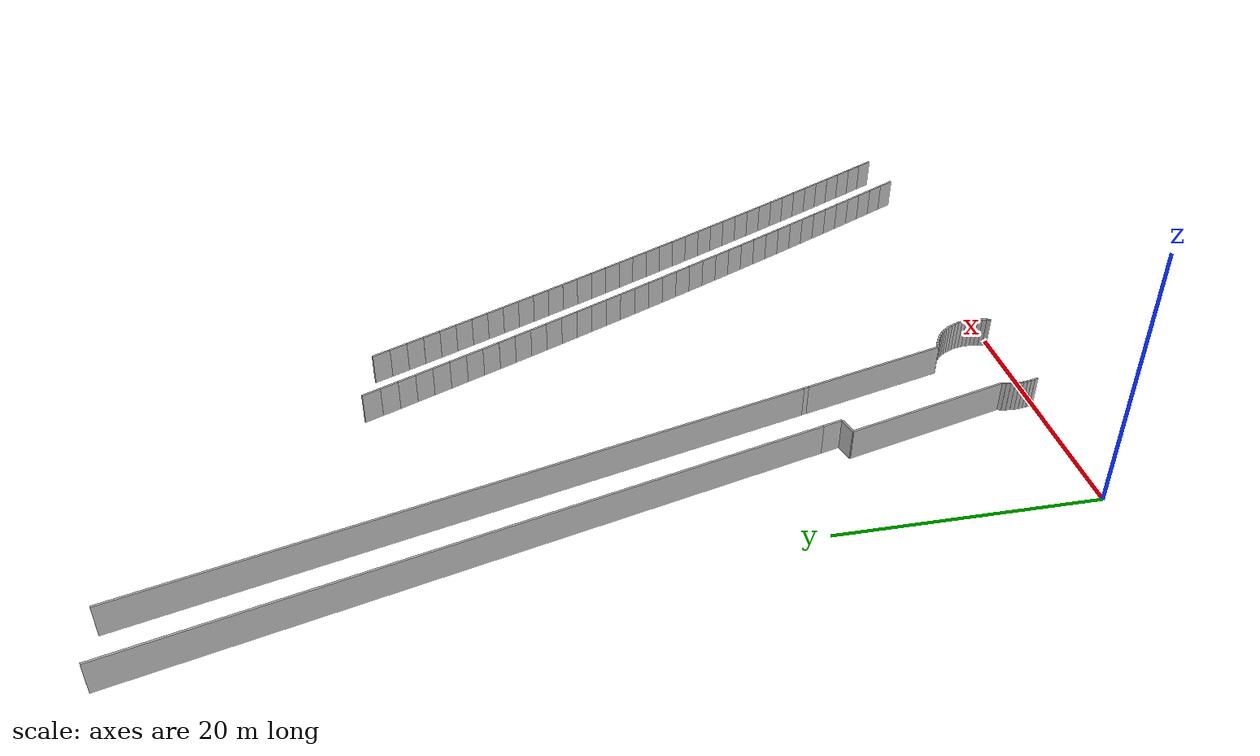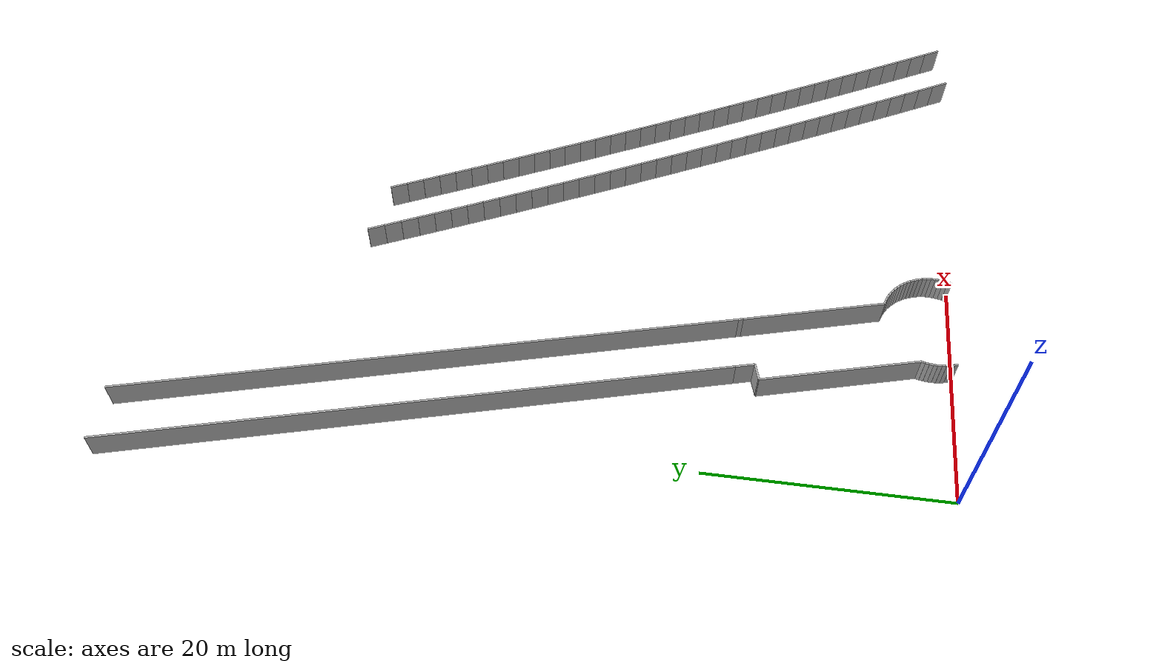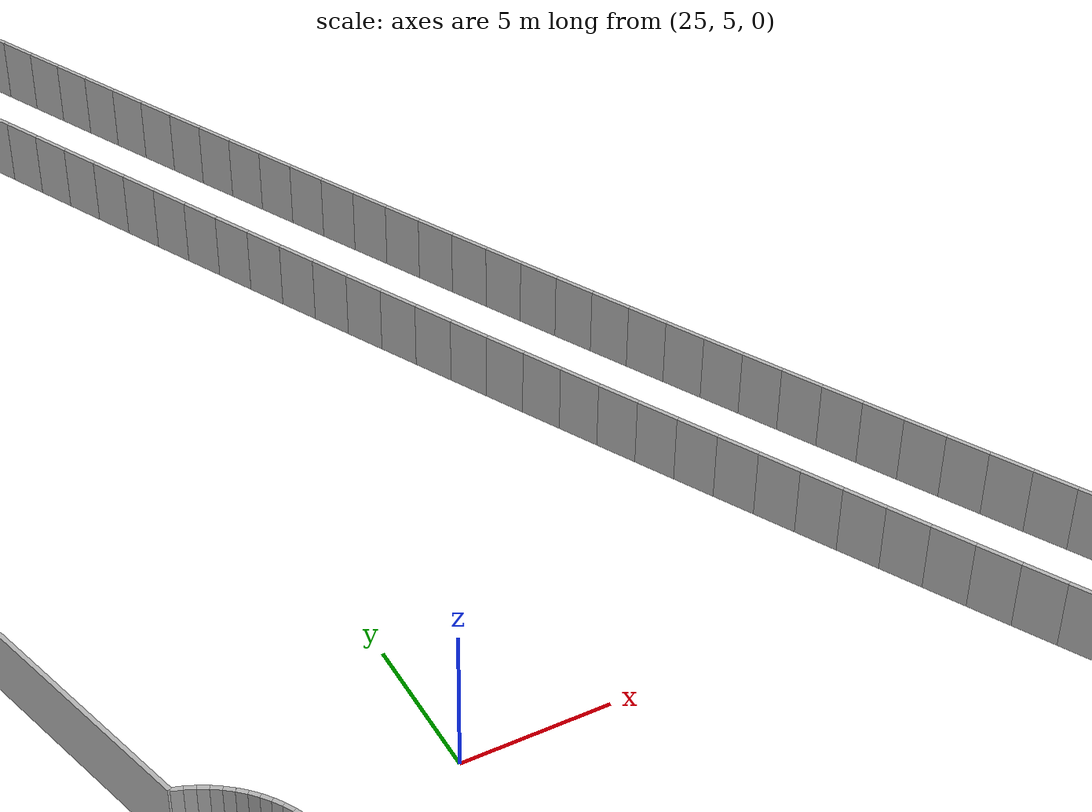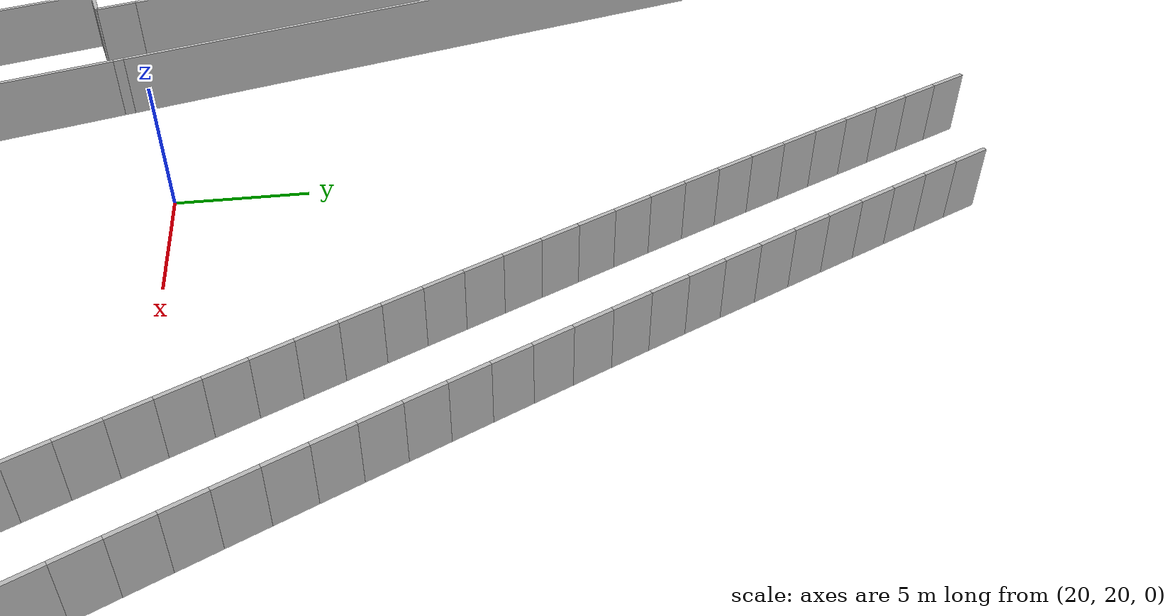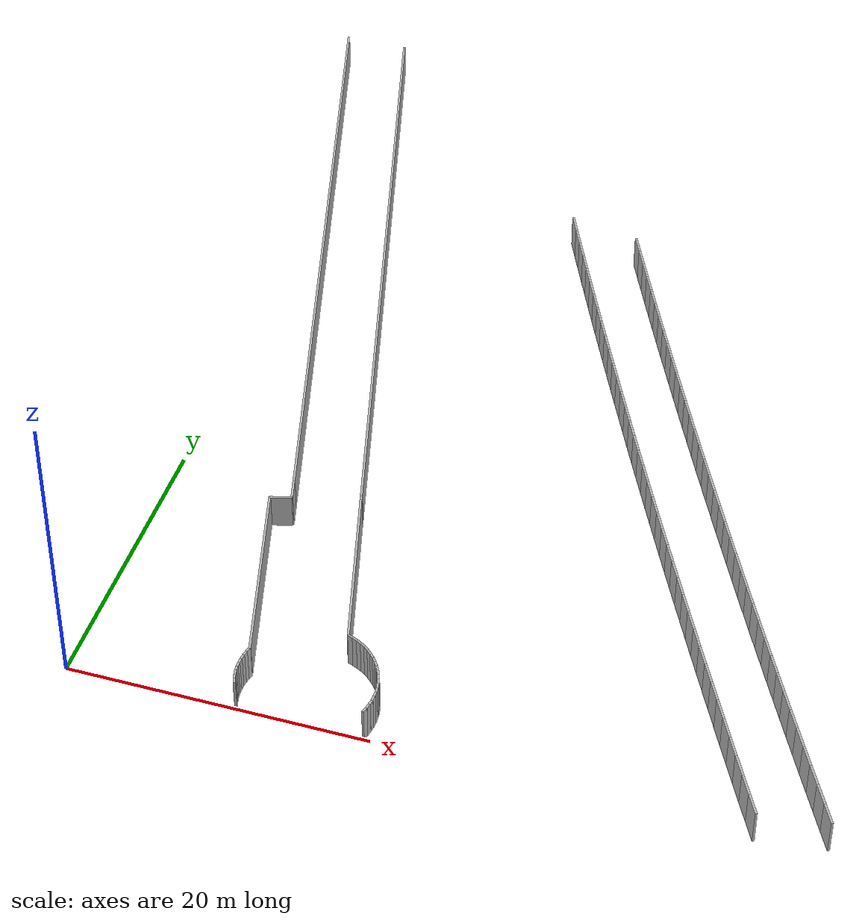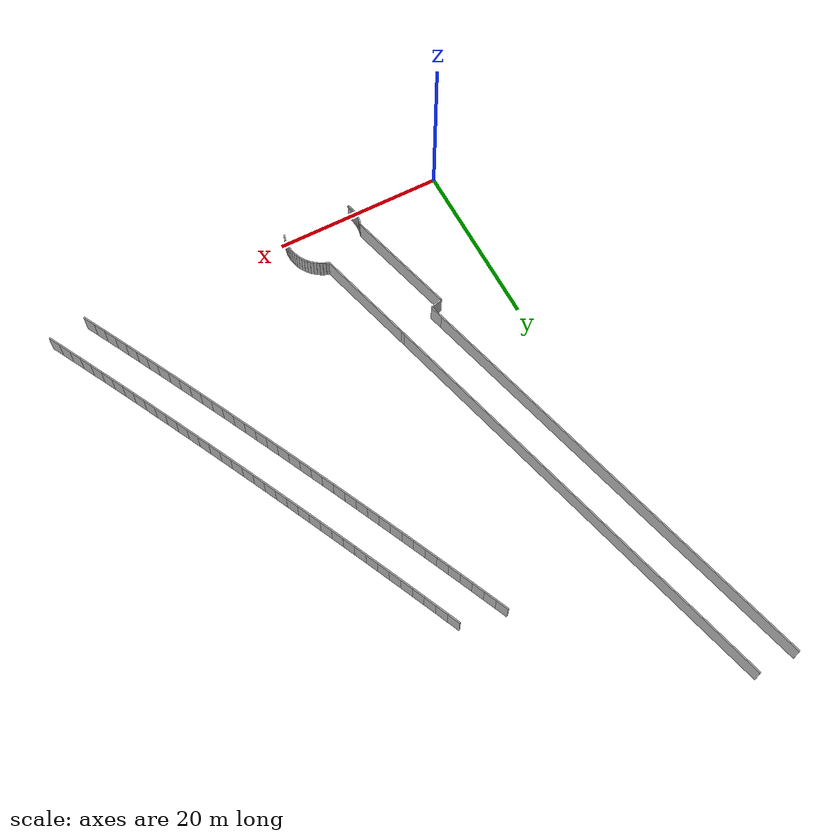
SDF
<?xml version="1.0" ?>
<sdf version="1.6">
  <model name="sps_0514">
    <pose frame="">0 0 0 0 -0 0</pose>
    <static>1</static>
    <self_collide>0</self_collide>
    <allow_auto_disable>0</allow_auto_disable>
    <link name="Wall270">
      <kinematic>0</kinematic>
      <gravity>1</gravity>
      <self_collide>0</self_collide>
      <collision name="collision">
        <geometry>
          <box>
            <size>0.404023 0.15 2.5</size>
          </box>
        </geometry>
        <pose frame="">0 0 0 0 -0 0</pose>
      </collision>
      <visual name="visual">
        <geometry>
          <box>
            <size>0.404023 0.15 2.5</size>
          </box>
        </geometry>
        <pose frame="">0 0 0 0 -0 0</pose>
        <cast_shadows>1</cast_shadows>
        <transparency>0.0</transparency>
      </visual>
      <pose frame="">13.4606 17.6979 1.25 0 -0 1.83141</pose>
    </link>
    <link name="Wall271">
      <kinematic>0</kinematic>
      <gravity>1</gravity>
      <self_collide>0</self_collide>
      <collision name="collision">
        <geometry>
          <box>
            <size>51.7473 0.15 2.5</size>
          </box>
        </geometry>
        <pose frame="">0 0 0 0 -0 0</pose>
      </collision>
      <visual name="visual">
        <geometry>
          <box>
            <size>51.7473 0.15 2.5</size>
          </box>
        </geometry>
        <pose frame="">0 0 0 0 -0 0</pose>
        <cast_shadows>1</cast_shadows>
        <transparency>0.0</transparency>
      </visual>
      <pose frame="">6.74169 42.8931 1.25 0 -0 1.83141</pose>
    </link>
    <link name="Wall329">
      <kinematic>0</kinematic>
      <gravity>1</gravity>
      <self_collide>0</self_collide>
      <collision name="collision">
        <geometry>
          <box>
            <size>1.61069 0.15 2.5</size>
          </box>
        </geometry>
        <pose frame="">0 0 0 0 -0 0</pose>
      </collision>
      <visual name="visual">
        <geometry>
          <box>
            <size>1.61069 0.15 2.5</size>
          </box>
        </geometry>
        <pose frame="">0 0 0 0 -0 0</pose>
        <cast_shadows>1</cast_shadows>
        <transparency>0.0</transparency>
      </visual>
      <pose frame="">8.9327 17.1149 1.25 0 -0 1.83117</pose>
    </link>
    <link name="Wall330">
      <kinematic>0</kinematic>
      <gravity>1</gravity>
      <self_collide>0</self_collide>
      <collision name="collision">
        <geometry>
          <box>
            <size>51.7441 0.15 2.5</size>
          </box>
        </geometry>
        <pose frame="">0 0 0 0 -0 0</pose>
      </collision>
      <visual name="visual">
        <geometry>
          <box>
            <size>51.7441 0.15 2.5</size>
          </box>
        </geometry>
        <pose frame="">0 0 0 0 -0 0</pose>
        <cast_shadows>1</cast_shadows>
        <transparency>0.0</transparency>
      </visual>
      <pose frame="">2.06472 42.8931 1.25 0 -0 1.83117</pose>
    </link>
    <link name="Wall1830">
      <kinematic>0</kinematic>
      <gravity>1</gravity>
      <self_collide>0</self_collide>
      <collision name="collision">
        <geometry>
          <box>
            <size>12.1005 0.15 2.5</size>
          </box>
        </geometry>
        <pose frame="">0 0 0 0 -0 0</pose>
      </collision>
      <visual name="visual">
        <geometry>
          <box>
            <size>12.1005 0.15 2.5</size>
          </box>
        </geometry>
        <pose frame="">0 0 0 0 -0 0</pose>
        <cast_shadows>1</cast_shadows>
        <transparency>0.0</transparency>
      </visual>
      <pose frame="">15.0825 11.6597 1.25 0 0 -1.30832</pose>
    </link>
    <link name="Wall1831">
      <kinematic>0</kinematic>
      <gravity>1</gravity>
      <self_collide>0</self_collide>
      <collision name="collision">
        <geometry>
          <box>
            <size>0.359052 0.15 2.5</size>
          </box>
        </geometry>
        <pose frame="">0 0 0 0 -0 0</pose>
      </collision>
      <visual name="visual">
        <geometry>
          <box>
            <size>0.359052 0.15 2.5</size>
          </box>
        </geometry>
        <pose frame="">0 0 0 0 -0 0</pose>
        <cast_shadows>1</cast_shadows>
        <transparency>0.0</transparency>
      </visual>
      <pose frame="">16.8222 5.75838 1.25 0 0 -0.330674</pose>
    </link>
    <link name="Wall1832">
      <kinematic>0</kinematic>
      <gravity>1</gravity>
      <self_collide>0</self_collide>
      <collision name="collision">
        <geometry>
          <box>
            <size>0.358996 0.15 2.5</size>
          </box>
        </geometry>
        <pose frame="">0 0 0 0 -0 0</pose>
      </collision>
      <visual name="visual">
        <geometry>
          <box>
            <size>0.358996 0.15 2.5</size>
          </box>
        </geometry>
        <pose frame="">0 0 0 0 -0 0</pose>
        <cast_shadows>1</cast_shadows>
        <transparency>0.0</transparency>
      </visual>
      <pose frame="">17.1565 5.6281 1.25 0 0 -0.412683</pose>
    </link>
    <link name="Wall1833">
      <kinematic>0</kinematic>
      <gravity>1</gravity>
      <self_collide>0</self_collide>
      <collision name="collision">
        <geometry>
          <box>
            <size>0.359076 0.15 2.5</size>
          </box>
        </geometry>
        <pose frame="">0 0 0 0 -0 0</pose>
      </collision>
      <visual name="visual">
        <geometry>
          <box>
            <size>0.359076 0.15 2.5</size>
          </box>
        </geometry>
        <pose frame="">0 0 0 0 -0 0</pose>
        <cast_shadows>1</cast_shadows>
        <transparency>0.0</transparency>
      </visual>
      <pose frame="">17.479 5.47099 1.25 0 0 -0.493907</pose>
    </link>
    <link name="Wall1834">
      <kinematic>0</kinematic>
      <gravity>1</gravity>
      <self_collide>0</self_collide>
      <collision name="collision">
        <geometry>
          <box>
            <size>0.359122 0.15 2.5</size>
          </box>
        </geometry>
        <pose frame="">0 0 0 0 -0 0</pose>
      </collision>
      <visual name="visual">
        <geometry>
          <box>
            <size>0.359122 0.15 2.5</size>
          </box>
        </geometry>
        <pose frame="">0 0 0 0 -0 0</pose>
        <cast_shadows>1</cast_shadows>
        <transparency>0.0</transparency>
      </visual>
      <pose frame="">17.7877 5.2881 1.25 0 0 -0.575841</pose>
    </link>
    <link name="Wall1835">
      <kinematic>0</kinematic>
      <gravity>1</gravity>
      <self_collide>0</self_collide>
      <collision name="collision">
        <geometry>
          <box>
            <size>0.35892 0.15 2.5</size>
          </box>
        </geometry>
        <pose frame="">0 0 0 0 -0 0</pose>
      </collision>
      <visual name="visual">
        <geometry>
          <box>
            <size>0.35892 0.15 2.5</size>
          </box>
        </geometry>
        <pose frame="">0 0 0 0 -0 0</pose>
        <cast_shadows>1</cast_shadows>
        <transparency>0.0</transparency>
      </visual>
      <pose frame="">18.0803 5.0807 1.25 0 0 -0.657106</pose>
    </link>
    <link name="Wall1836">
      <kinematic>0</kinematic>
      <gravity>1</gravity>
      <self_collide>0</self_collide>
      <collision name="collision">
        <geometry>
          <box>
            <size>0.359021 0.15 2.5</size>
          </box>
        </geometry>
        <pose frame="">0 0 0 0 -0 0</pose>
      </collision>
      <visual name="visual">
        <geometry>
          <box>
            <size>0.359021 0.15 2.5</size>
          </box>
        </geometry>
        <pose frame="">0 0 0 0 -0 0</pose>
        <cast_shadows>1</cast_shadows>
        <transparency>0.0</transparency>
      </visual>
      <pose frame="">18.355 4.85008 1.25 0 0 -0.739702</pose>
    </link>
    <link name="Wall1837">
      <kinematic>0</kinematic>
      <gravity>1</gravity>
      <self_collide>0</self_collide>
      <collision name="collision">
        <geometry>
          <box>
            <size>0.358995 0.15 2.5</size>
          </box>
        </geometry>
        <pose frame="">0 0 0 0 -0 0</pose>
      </collision>
      <visual name="visual">
        <geometry>
          <box>
            <size>0.358995 0.15 2.5</size>
          </box>
        </geometry>
        <pose frame="">0 0 0 0 -0 0</pose>
        <cast_shadows>1</cast_shadows>
        <transparency>0.0</transparency>
      </visual>
      <pose frame="">18.61 4.59779 1.25 0 0 -0.820389</pose>
    </link>
    <link name="Wall1838">
      <kinematic>0</kinematic>
      <gravity>1</gravity>
      <self_collide>0</self_collide>
      <collision name="collision">
        <geometry>
          <box>
            <size>0.359109 0.15 2.5</size>
          </box>
        </geometry>
        <pose frame="">0 0 0 0 -0 0</pose>
      </collision>
      <visual name="visual">
        <geometry>
          <box>
            <size>0.359109 0.15 2.5</size>
          </box>
        </geometry>
        <pose frame="">0 0 0 0 -0 0</pose>
        <cast_shadows>1</cast_shadows>
        <transparency>0.0</transparency>
      </visual>
      <pose frame="">18.8437 4.32561 1.25 0 0 -0.90224</pose>
    </link>
    <link name="Wall1839">
      <kinematic>0</kinematic>
      <gravity>1</gravity>
      <self_collide>0</self_collide>
      <collision name="collision">
        <geometry>
          <box>
            <size>0.359062 0.15 2.5</size>
          </box>
        </geometry>
        <pose frame="">0 0 0 0 -0 0</pose>
      </collision>
      <visual name="visual">
        <geometry>
          <box>
            <size>0.359062 0.15 2.5</size>
          </box>
        </geometry>
        <pose frame="">0 0 0 0 -0 0</pose>
        <cast_shadows>1</cast_shadows>
        <transparency>0.0</transparency>
      </visual>
      <pose frame="">19.0544 4.0352 1.25 0 0 -0.984067</pose>
    </link>
    <link name="Wall1840">
      <kinematic>0</kinematic>
      <gravity>1</gravity>
      <self_collide>0</self_collide>
      <collision name="collision">
        <geometry>
          <box>
            <size>0.358927 0.15 2.5</size>
          </box>
        </geometry>
        <pose frame="">0 0 0 0 -0 0</pose>
      </collision>
      <visual name="visual">
        <geometry>
          <box>
            <size>0.358927 0.15 2.5</size>
          </box>
        </geometry>
        <pose frame="">0 0 0 0 -0 0</pose>
        <cast_shadows>1</cast_shadows>
        <transparency>0.0</transparency>
      </visual>
      <pose frame="">19.2407 3.72868 1.25 0 0 -1.06523</pose>
    </link>
    <link name="Wall1841">
      <kinematic>0</kinematic>
      <gravity>1</gravity>
      <self_collide>0</self_collide>
      <collision name="collision">
        <geometry>
          <box>
            <size>0.359119 0.15 2.5</size>
          </box>
        </geometry>
        <pose frame="">0 0 0 0 -0 0</pose>
      </collision>
      <visual name="visual">
        <geometry>
          <box>
            <size>0.359119 0.15 2.5</size>
          </box>
        </geometry>
        <pose frame="">0 0 0 0 -0 0</pose>
        <cast_shadows>1</cast_shadows>
        <transparency>0.0</transparency>
      </visual>
      <pose frame="">19.4015 3.40797 1.25 0 0 -1.14729</pose>
    </link>
    <link name="Wall1842">
      <kinematic>0</kinematic>
      <gravity>1</gravity>
      <self_collide>0</self_collide>
      <collision name="collision">
        <geometry>
          <box>
            <size>0.359057 0.15 2.5</size>
          </box>
        </geometry>
        <pose frame="">0 0 0 0 -0 0</pose>
      </collision>
      <visual name="visual">
        <geometry>
          <box>
            <size>0.359057 0.15 2.5</size>
          </box>
        </geometry>
        <pose frame="">0 0 0 0 -0 0</pose>
        <cast_shadows>1</cast_shadows>
        <transparency>0.0</transparency>
      </visual>
      <pose frame="">19.5355 3.07518 1.25 0 0 -1.22824</pose>
    </link>
    <link name="Wall1843">
      <kinematic>0</kinematic>
      <gravity>1</gravity>
      <self_collide>0</self_collide>
      <collision name="collision">
        <geometry>
          <box>
            <size>0.359079 0.15 2.5</size>
          </box>
        </geometry>
        <pose frame="">0 0 0 0 -0 0</pose>
      </collision>
      <visual name="visual">
        <geometry>
          <box>
            <size>0.359079 0.15 2.5</size>
          </box>
        </geometry>
        <pose frame="">0 0 0 0 -0 0</pose>
        <cast_shadows>1</cast_shadows>
        <transparency>0.0</transparency>
      </visual>
      <pose frame="">19.6421 2.73259 1.25 0 0 -1.31052</pose>
    </link>
    <link name="Wall1844">
      <kinematic>0</kinematic>
      <gravity>1</gravity>
      <self_collide>0</self_collide>
      <collision name="collision">
        <geometry>
          <box>
            <size>0.359147 0.15 2.5</size>
          </box>
        </geometry>
        <pose frame="">0 0 0 0 -0 0</pose>
      </collision>
      <visual name="visual">
        <geometry>
          <box>
            <size>0.359147 0.15 2.5</size>
          </box>
        </geometry>
        <pose frame="">0 0 0 0 -0 0</pose>
        <cast_shadows>1</cast_shadows>
        <transparency>0.0</transparency>
      </visual>
      <pose frame="">19.7203 2.3824 1.25 0 0 -1.39157</pose>
    </link>
    <link name="Wall1845">
      <kinematic>0</kinematic>
      <gravity>1</gravity>
      <self_collide>0</self_collide>
      <collision name="collision">
        <geometry>
          <box>
            <size>0.359111 0.15 2.5</size>
          </box>
        </geometry>
        <pose frame="">0 0 0 0 -0 0</pose>
      </collision>
      <visual name="visual">
        <geometry>
          <box>
            <size>0.359111 0.15 2.5</size>
          </box>
        </geometry>
        <pose frame="">0 0 0 0 -0 0</pose>
        <cast_shadows>1</cast_shadows>
        <transparency>0.0</transparency>
      </visual>
      <pose frame="">19.7697 2.02699 1.25 0 0 -1.47377</pose>
    </link>
    <link name="Wall1846">
      <kinematic>0</kinematic>
      <gravity>1</gravity>
      <self_collide>0</self_collide>
      <collision name="collision">
        <geometry>
          <box>
            <size>0.359053 0.15 2.5</size>
          </box>
        </geometry>
        <pose frame="">0 0 0 0 -0 0</pose>
      </collision>
      <visual name="visual">
        <geometry>
          <box>
            <size>0.359053 0.15 2.5</size>
          </box>
        </geometry>
        <pose frame="">0 0 0 0 -0 0</pose>
        <cast_shadows>1</cast_shadows>
        <transparency>0.0</transparency>
      </visual>
      <pose frame="">19.7899 1.66878 1.25 0 0 -1.55516</pose>
    </link>
    <link name="Wall1847">
      <kinematic>0</kinematic>
      <gravity>1</gravity>
      <self_collide>0</self_collide>
      <collision name="collision">
        <geometry>
          <box>
            <size>0.358944 0.15 2.5</size>
          </box>
        </geometry>
        <pose frame="">0 0 0 0 -0 0</pose>
      </collision>
      <visual name="visual">
        <geometry>
          <box>
            <size>0.358944 0.15 2.5</size>
          </box>
        </geometry>
        <pose frame="">0 0 0 0 -0 0</pose>
        <cast_shadows>1</cast_shadows>
        <transparency>0.0</transparency>
      </visual>
      <pose frame="">19.7808 1.31019 1.25 0 0 -1.63716</pose>
    </link>
    <link name="Wall1848">
      <kinematic>0</kinematic>
      <gravity>1</gravity>
      <self_collide>0</self_collide>
      <collision name="collision">
        <geometry>
          <box>
            <size>0.359136 0.15 2.5</size>
          </box>
        </geometry>
        <pose frame="">0 0 0 0 -0 0</pose>
      </collision>
      <visual name="visual">
        <geometry>
          <box>
            <size>0.359136 0.15 2.5</size>
          </box>
        </geometry>
        <pose frame="">0 0 0 0 -0 0</pose>
        <cast_shadows>1</cast_shadows>
        <transparency>0.0</transparency>
      </visual>
      <pose frame="">19.7425 0.953505 1.25 0 0 -1.71851</pose>
    </link>
    <link name="Wall1849">
      <kinematic>0</kinematic>
      <gravity>1</gravity>
      <self_collide>0</self_collide>
      <collision name="collision">
        <geometry>
          <box>
            <size>0.358993 0.15 2.5</size>
          </box>
        </geometry>
        <pose frame="">0 0 0 0 -0 0</pose>
      </collision>
      <visual name="visual">
        <geometry>
          <box>
            <size>0.358993 0.15 2.5</size>
          </box>
        </geometry>
        <pose frame="">0 0 0 0 -0 0</pose>
        <cast_shadows>1</cast_shadows>
        <transparency>0.0</transparency>
      </visual>
      <pose frame="">19.6753 0.601088 1.25 0 0 -1.79994</pose>
    </link>
    <link name="Wall1850">
      <kinematic>0</kinematic>
      <gravity>1</gravity>
      <self_collide>0</self_collide>
      <collision name="collision">
        <geometry>
          <box>
            <size>0.359076 0.15 2.5</size>
          </box>
        </geometry>
        <pose frame="">0 0 0 0 -0 0</pose>
      </collision>
      <visual name="visual">
        <geometry>
          <box>
            <size>0.359076 0.15 2.5</size>
          </box>
        </geometry>
        <pose frame="">0 0 0 0 -0 0</pose>
        <cast_shadows>1</cast_shadows>
        <transparency>0.0</transparency>
      </visual>
      <pose frame="">19.5795 0.255385 1.25 0 0 -1.88228</pose>
    </link>
    <link name="Wall1877">
      <kinematic>0</kinematic>
      <gravity>1</gravity>
      <self_collide>0</self_collide>
      <collision name="collision">
        <geometry>
          <box>
            <size>0.335259 0.15 2.5</size>
          </box>
        </geometry>
        <pose frame="">0 0 0 0 -0 0</pose>
      </collision>
      <visual name="visual">
        <geometry>
          <box>
            <size>0.335259 0.15 2.5</size>
          </box>
        </geometry>
        <pose frame="">0 0 0 0 -0 0</pose>
        <cast_shadows>1</cast_shadows>
        <transparency>0.0</transparency>
      </visual>
      <pose frame="">11.2461 0.148513 1.25 0 -0 1.90775</pose>
    </link>
    <link name="Wall1878">
      <kinematic>0</kinematic>
      <gravity>1</gravity>
      <self_collide>0</self_collide>
      <collision name="collision">
        <geometry>
          <box>
            <size>0.335064 0.15 2.5</size>
          </box>
        </geometry>
        <pose frame="">0 0 0 0 -0 0</pose>
      </collision>
      <visual name="visual">
        <geometry>
          <box>
            <size>0.335064 0.15 2.5</size>
          </box>
        </geometry>
        <pose frame="">0 0 0 0 -0 0</pose>
        <cast_shadows>1</cast_shadows>
        <transparency>0.0</transparency>
      </visual>
      <pose frame="">11.1475 0.468612 1.25 0 -0 1.83093</pose>
    </link>
    <link name="Wall1879">
      <kinematic>0</kinematic>
      <gravity>1</gravity>
      <self_collide>0</self_collide>
      <collision name="collision">
        <geometry>
          <box>
            <size>0.33526 0.15 2.5</size>
          </box>
        </geometry>
        <pose frame="">0 0 0 0 -0 0</pose>
      </collision>
      <visual name="visual">
        <geometry>
          <box>
            <size>0.33526 0.15 2.5</size>
          </box>
        </geometry>
        <pose frame="">0 0 0 0 -0 0</pose>
        <cast_shadows>1</cast_shadows>
        <transparency>0.0</transparency>
      </visual>
      <pose frame="">11.0738 0.795302 1.25 0 -0 1.75498</pose>
    </link>
    <link name="Wall1880">
      <kinematic>0</kinematic>
      <gravity>1</gravity>
      <self_collide>0</self_collide>
      <collision name="collision">
        <geometry>
          <box>
            <size>0.335131 0.15 2.5</size>
          </box>
        </geometry>
        <pose frame="">0 0 0 0 -0 0</pose>
      </collision>
      <visual name="visual">
        <geometry>
          <box>
            <size>0.335131 0.15 2.5</size>
          </box>
        </geometry>
        <pose frame="">0 0 0 0 -0 0</pose>
        <cast_shadows>1</cast_shadows>
        <transparency>0.0</transparency>
      </visual>
      <pose frame="">11.025 1.12669 1.25 0 -0 1.67846</pose>
    </link>
    <link name="Wall1881">
      <kinematic>0</kinematic>
      <gravity>1</gravity>
      <self_collide>0</self_collide>
      <collision name="collision">
        <geometry>
          <box>
            <size>0.335379 0.15 2.5</size>
          </box>
        </geometry>
        <pose frame="">0 0 0 0 -0 0</pose>
      </collision>
      <visual name="visual">
        <geometry>
          <box>
            <size>0.335379 0.15 2.5</size>
          </box>
        </geometry>
        <pose frame="">0 0 0 0 -0 0</pose>
        <cast_shadows>1</cast_shadows>
        <transparency>0.0</transparency>
      </visual>
      <pose frame="">11.0016 1.46089 1.25 0 -0 1.60301</pose>
    </link>
    <link name="Wall1882">
      <kinematic>0</kinematic>
      <gravity>1</gravity>
      <self_collide>0</self_collide>
      <collision name="collision">
        <geometry>
          <box>
            <size>0.335114 0.15 2.5</size>
          </box>
        </geometry>
        <pose frame="">0 0 0 0 -0 0</pose>
      </collision>
      <visual name="visual">
        <geometry>
          <box>
            <size>0.335114 0.15 2.5</size>
          </box>
        </geometry>
        <pose frame="">0 0 0 0 -0 0</pose>
        <cast_shadows>1</cast_shadows>
        <transparency>0.0</transparency>
      </visual>
      <pose frame="">11.0037 1.79588 1.25 0 -0 1.52598</pose>
    </link>
    <link name="Wall1883">
      <kinematic>0</kinematic>
      <gravity>1</gravity>
      <self_collide>0</self_collide>
      <collision name="collision">
        <geometry>
          <box>
            <size>0.335268 0.15 2.5</size>
          </box>
        </geometry>
        <pose frame="">0 0 0 0 -0 0</pose>
      </collision>
      <visual name="visual">
        <geometry>
          <box>
            <size>0.335268 0.15 2.5</size>
          </box>
        </geometry>
        <pose frame="">0 0 0 0 -0 0</pose>
        <cast_shadows>1</cast_shadows>
        <transparency>0.0</transparency>
      </visual>
      <pose frame="">11.0315 2.12968 1.25 0 -0 1.44999</pose>
    </link>
    <link name="Wall1884">
      <kinematic>0</kinematic>
      <gravity>1</gravity>
      <self_collide>0</self_collide>
      <collision name="collision">
        <geometry>
          <box>
            <size>0.335279 0.15 2.5</size>
          </box>
        </geometry>
        <pose frame="">0 0 0 0 -0 0</pose>
      </collision>
      <visual name="visual">
        <geometry>
          <box>
            <size>0.335279 0.15 2.5</size>
          </box>
        </geometry>
        <pose frame="">0 0 0 0 -0 0</pose>
        <cast_shadows>1</cast_shadows>
        <transparency>0.0</transparency>
      </visual>
      <pose frame="">11.0845 2.46049 1.25 0 -0 1.37383</pose>
    </link>
    <link name="Wall1885">
      <kinematic>0</kinematic>
      <gravity>1</gravity>
      <self_collide>0</self_collide>
      <collision name="collision">
        <geometry>
          <box>
            <size>0.335232 0.15 2.5</size>
          </box>
        </geometry>
        <pose frame="">0 0 0 0 -0 0</pose>
      </collision>
      <visual name="visual">
        <geometry>
          <box>
            <size>0.335232 0.15 2.5</size>
          </box>
        </geometry>
        <pose frame="">0 0 0 0 -0 0</pose>
        <cast_shadows>1</cast_shadows>
        <transparency>0.0</transparency>
      </visual>
      <pose frame="">11.1625 2.7863 1.25 0 -0 1.29777</pose>
    </link>
    <link name="Wall1886">
      <kinematic>0</kinematic>
      <gravity>1</gravity>
      <self_collide>0</self_collide>
      <collision name="collision">
        <geometry>
          <box>
            <size>13.4709 0.15 2.5</size>
          </box>
        </geometry>
        <pose frame="">0 0 0 0 -0 0</pose>
      </collision>
      <visual name="visual">
        <geometry>
          <box>
            <size>13.4709 0.15 2.5</size>
          </box>
        </geometry>
        <pose frame="">0 0 0 0 -0 0</pose>
        <cast_shadows>1</cast_shadows>
        <transparency>0.0</transparency>
      </visual>
      <pose frame="">9.47326 9.45601 1.25 0 -0 1.83123</pose>
    </link>
    <link name="Wall1887">
      <kinematic>0</kinematic>
      <gravity>1</gravity>
      <self_collide>0</self_collide>
      <collision name="collision">
        <geometry>
          <box>
            <size>1.44982 0.15 2.5</size>
          </box>
        </geometry>
        <pose frame="">0 0 0 0 -0 0</pose>
      </collision>
      <visual name="visual">
        <geometry>
          <box>
            <size>1.44982 0.15 2.5</size>
          </box>
        </geometry>
        <pose frame="">0 0 0 0 -0 0</pose>
        <cast_shadows>1</cast_shadows>
        <transparency>0.0</transparency>
      </visual>
      <pose frame="">8.43944 16.1505 1.25 0 -0 0.259754</pose>
    </link>
    <link name="Wall8285">
      <kinematic>0</kinematic>
      <gravity>1</gravity>
      <self_collide>0</self_collide>
      <collision name="collision">
        <geometry>
          <box>
            <size>1.49895 0.15 2.5</size>
          </box>
        </geometry>
        <pose frame="">0 0 0 0 -0 0</pose>
      </collision>
      <visual name="visual">
        <geometry>
          <box>
            <size>1.49895 0.15 2.5</size>
          </box>
        </geometry>
        <pose frame="">0 0 0 0 -0 0</pose>
        <cast_shadows>1</cast_shadows>
        <transparency>0.0</transparency>
      </visual>
      <pose frame="">19.113 49.9425 1.25 0 0 -1.14451</pose>
    </link>
    <link name="Wall8286">
      <kinematic>0</kinematic>
      <gravity>1</gravity>
      <self_collide>0</self_collide>
      <collision name="collision">
        <geometry>
          <box>
            <size>1.49904 0.15 2.5</size>
          </box>
        </geometry>
        <pose frame="">0 0 0 0 -0 0</pose>
      </collision>
      <visual name="visual">
        <geometry>
          <box>
            <size>1.49904 0.15 2.5</size>
          </box>
        </geometry>
        <pose frame="">0 0 0 0 -0 0</pose>
        <cast_shadows>1</cast_shadows>
        <transparency>0.0</transparency>
      </visual>
      <pose frame="">19.7338 48.5781 1.25 0 0 -1.1431</pose>
    </link>
    <link name="Wall8287">
      <kinematic>0</kinematic>
      <gravity>1</gravity>
      <self_collide>0</self_collide>
      <collision name="collision">
        <geometry>
          <box>
            <size>1.49879 0.15 2.5</size>
          </box>
        </geometry>
        <pose frame="">0 0 0 0 -0 0</pose>
      </collision>
      <visual name="visual">
        <geometry>
          <box>
            <size>1.49879 0.15 2.5</size>
          </box>
        </geometry>
        <pose frame="">0 0 0 0 -0 0</pose>
        <cast_shadows>1</cast_shadows>
        <transparency>0.0</transparency>
      </visual>
      <pose frame="">20.3566 47.2147 1.25 0 0 -1.1415</pose>
    </link>
    <link name="Wall8288">
      <kinematic>0</kinematic>
      <gravity>1</gravity>
      <self_collide>0</self_collide>
      <collision name="collision">
        <geometry>
          <box>
            <size>1.49904 0.15 2.5</size>
          </box>
        </geometry>
        <pose frame="">0 0 0 0 -0 0</pose>
      </collision>
      <visual name="visual">
        <geometry>
          <box>
            <size>1.49904 0.15 2.5</size>
          </box>
        </geometry>
        <pose frame="">0 0 0 0 -0 0</pose>
        <cast_shadows>1</cast_shadows>
        <transparency>0.0</transparency>
      </visual>
      <pose frame="">20.9816 45.8523 1.25 0 0 -1.13988</pose>
    </link>
    <link name="Wall8289">
      <kinematic>0</kinematic>
      <gravity>1</gravity>
      <self_collide>0</self_collide>
      <collision name="collision">
        <geometry>
          <box>
            <size>1.49888 0.15 2.5</size>
          </box>
        </geometry>
        <pose frame="">0 0 0 0 -0 0</pose>
      </collision>
      <visual name="visual">
        <geometry>
          <box>
            <size>1.49888 0.15 2.5</size>
          </box>
        </geometry>
        <pose frame="">0 0 0 0 -0 0</pose>
        <cast_shadows>1</cast_shadows>
        <transparency>0.0</transparency>
      </visual>
      <pose frame="">21.6088 44.4909 1.25 0 0 -1.13817</pose>
    </link>
    <link name="Wall8290">
      <kinematic>0</kinematic>
      <gravity>1</gravity>
      <self_collide>0</self_collide>
      <collision name="collision">
        <geometry>
          <box>
            <size>1.49881 0.15 2.5</size>
          </box>
        </geometry>
        <pose frame="">0 0 0 0 -0 0</pose>
      </collision>
      <visual name="visual">
        <geometry>
          <box>
            <size>1.49881 0.15 2.5</size>
          </box>
        </geometry>
        <pose frame="">0 0 0 0 -0 0</pose>
        <cast_shadows>1</cast_shadows>
        <transparency>0.0</transparency>
      </visual>
      <pose frame="">22.2382 43.1306 1.25 0 0 -1.13671</pose>
    </link>
    <link name="Wall8291">
      <kinematic>0</kinematic>
      <gravity>1</gravity>
      <self_collide>0</self_collide>
      <collision name="collision">
        <geometry>
          <box>
            <size>1.49904 0.15 2.5</size>
          </box>
        </geometry>
        <pose frame="">0 0 0 0 -0 0</pose>
      </collision>
      <visual name="visual">
        <geometry>
          <box>
            <size>1.49904 0.15 2.5</size>
          </box>
        </geometry>
        <pose frame="">0 0 0 0 -0 0</pose>
        <cast_shadows>1</cast_shadows>
        <transparency>0.0</transparency>
      </visual>
      <pose frame="">22.8697 41.7712 1.25 0 0 -1.13512</pose>
    </link>
    <link name="Wall8292">
      <kinematic>0</kinematic>
      <gravity>1</gravity>
      <self_collide>0</self_collide>
      <collision name="collision">
        <geometry>
          <box>
            <size>1.49886 0.15 2.5</size>
          </box>
        </geometry>
        <pose frame="">0 0 0 0 -0 0</pose>
      </collision>
      <visual name="visual">
        <geometry>
          <box>
            <size>1.49886 0.15 2.5</size>
          </box>
        </geometry>
        <pose frame="">0 0 0 0 -0 0</pose>
        <cast_shadows>1</cast_shadows>
        <transparency>0.0</transparency>
      </visual>
      <pose frame="">23.5035 40.4128 1.25 0 0 -1.13345</pose>
    </link>
    <link name="Wall8293">
      <kinematic>0</kinematic>
      <gravity>1</gravity>
      <self_collide>0</self_collide>
      <collision name="collision">
        <geometry>
          <box>
            <size>1.49897 0.15 2.5</size>
          </box>
        </geometry>
        <pose frame="">0 0 0 0 -0 0</pose>
      </collision>
      <visual name="visual">
        <geometry>
          <box>
            <size>1.49897 0.15 2.5</size>
          </box>
        </geometry>
        <pose frame="">0 0 0 0 -0 0</pose>
        <cast_shadows>1</cast_shadows>
        <transparency>0.0</transparency>
      </visual>
      <pose frame="">24.1393 39.0554 1.25 0 0 -1.13204</pose>
    </link>
    <link name="Wall8294">
      <kinematic>0</kinematic>
      <gravity>1</gravity>
      <self_collide>0</self_collide>
      <collision name="collision">
        <geometry>
          <box>
            <size>1.49896 0.15 2.5</size>
          </box>
        </geometry>
        <pose frame="">0 0 0 0 -0 0</pose>
      </collision>
      <visual name="visual">
        <geometry>
          <box>
            <size>1.49896 0.15 2.5</size>
          </box>
        </geometry>
        <pose frame="">0 0 0 0 -0 0</pose>
        <cast_shadows>1</cast_shadows>
        <transparency>0.0</transparency>
      </visual>
      <pose frame="">24.7773 37.699 1.25 0 0 -1.13024</pose>
    </link>
    <link name="Wall8295">
      <kinematic>0</kinematic>
      <gravity>1</gravity>
      <self_collide>0</self_collide>
      <collision name="collision">
        <geometry>
          <box>
            <size>1.49903 0.15 2.5</size>
          </box>
        </geometry>
        <pose frame="">0 0 0 0 -0 0</pose>
      </collision>
      <visual name="visual">
        <geometry>
          <box>
            <size>1.49903 0.15 2.5</size>
          </box>
        </geometry>
        <pose frame="">0 0 0 0 -0 0</pose>
        <cast_shadows>1</cast_shadows>
        <transparency>0.0</transparency>
      </visual>
      <pose frame="">25.4175 36.3436 1.25 0 0 -1.12882</pose>
    </link>
    <link name="Wall8296">
      <kinematic>0</kinematic>
      <gravity>1</gravity>
      <self_collide>0</self_collide>
      <collision name="collision">
        <geometry>
          <box>
            <size>1.49884 0.15 2.5</size>
          </box>
        </geometry>
        <pose frame="">0 0 0 0 -0 0</pose>
      </collision>
      <visual name="visual">
        <geometry>
          <box>
            <size>1.49884 0.15 2.5</size>
          </box>
        </geometry>
        <pose frame="">0 0 0 0 -0 0</pose>
        <cast_shadows>1</cast_shadows>
        <transparency>0.0</transparency>
      </visual>
      <pose frame="">26.0597 34.9892 1.25 0 0 -1.12727</pose>
    </link>
    <link name="Wall8297">
      <kinematic>0</kinematic>
      <gravity>1</gravity>
      <self_collide>0</self_collide>
      <collision name="collision">
        <geometry>
          <box>
            <size>1.49912 0.15 2.5</size>
          </box>
        </geometry>
        <pose frame="">0 0 0 0 -0 0</pose>
      </collision>
      <visual name="visual">
        <geometry>
          <box>
            <size>1.49912 0.15 2.5</size>
          </box>
        </geometry>
        <pose frame="">0 0 0 0 -0 0</pose>
        <cast_shadows>1</cast_shadows>
        <transparency>0.0</transparency>
      </visual>
      <pose frame="">26.7041 33.6358 1.25 0 0 -1.12556</pose>
    </link>
    <link name="Wall8298">
      <kinematic>0</kinematic>
      <gravity>1</gravity>
      <self_collide>0</self_collide>
      <collision name="collision">
        <geometry>
          <box>
            <size>1.49891 0.15 2.5</size>
          </box>
        </geometry>
        <pose frame="">0 0 0 0 -0 0</pose>
      </collision>
      <visual name="visual">
        <geometry>
          <box>
            <size>1.49891 0.15 2.5</size>
          </box>
        </geometry>
        <pose frame="">0 0 0 0 -0 0</pose>
        <cast_shadows>1</cast_shadows>
        <transparency>0.0</transparency>
      </visual>
      <pose frame="">27.3507 32.2834 1.25 0 0 -1.12405</pose>
    </link>
    <link name="Wall8299">
      <kinematic>0</kinematic>
      <gravity>1</gravity>
      <self_collide>0</self_collide>
      <collision name="collision">
        <geometry>
          <box>
            <size>1.49891 0.15 2.5</size>
          </box>
        </geometry>
        <pose frame="">0 0 0 0 -0 0</pose>
      </collision>
      <visual name="visual">
        <geometry>
          <box>
            <size>1.49891 0.15 2.5</size>
          </box>
        </geometry>
        <pose frame="">0 0 0 0 -0 0</pose>
        <cast_shadows>1</cast_shadows>
        <transparency>0.0</transparency>
      </visual>
      <pose frame="">27.9993 30.9321 1.25 0 0 -1.12256</pose>
    </link>
    <link name="Wall8300">
      <kinematic>0</kinematic>
      <gravity>1</gravity>
      <self_collide>0</self_collide>
      <collision name="collision">
        <geometry>
          <box>
            <size>1.499 0.15 2.5</size>
          </box>
        </geometry>
        <pose frame="">0 0 0 0 -0 0</pose>
      </collision>
      <visual name="visual">
        <geometry>
          <box>
            <size>1.499 0.15 2.5</size>
          </box>
        </geometry>
        <pose frame="">0 0 0 0 -0 0</pose>
        <cast_shadows>1</cast_shadows>
        <transparency>0.0</transparency>
      </visual>
      <pose frame="">28.65 29.5818 1.25 0 0 -1.12082</pose>
    </link>
    <link name="Wall8301">
      <kinematic>0</kinematic>
      <gravity>1</gravity>
      <self_collide>0</self_collide>
      <collision name="collision">
        <geometry>
          <box>
            <size>1.49895 0.15 2.5</size>
          </box>
        </geometry>
        <pose frame="">0 0 0 0 -0 0</pose>
      </collision>
      <visual name="visual">
        <geometry>
          <box>
            <size>1.49895 0.15 2.5</size>
          </box>
        </geometry>
        <pose frame="">0 0 0 0 -0 0</pose>
        <cast_shadows>1</cast_shadows>
        <transparency>0.0</transparency>
      </visual>
      <pose frame="">29.303 28.2325 1.25 0 0 -1.11931</pose>
    </link>
    <link name="Wall8302">
      <kinematic>0</kinematic>
      <gravity>1</gravity>
      <self_collide>0</self_collide>
      <collision name="collision">
        <geometry>
          <box>
            <size>1.499 0.15 2.5</size>
          </box>
        </geometry>
        <pose frame="">0 0 0 0 -0 0</pose>
      </collision>
      <visual name="visual">
        <geometry>
          <box>
            <size>1.499 0.15 2.5</size>
          </box>
        </geometry>
        <pose frame="">0 0 0 0 -0 0</pose>
        <cast_shadows>1</cast_shadows>
        <transparency>0.0</transparency>
      </visual>
      <pose frame="">29.958 26.8842 1.25 0 0 -1.11784</pose>
    </link>
    <link name="Wall8303">
      <kinematic>0</kinematic>
      <gravity>1</gravity>
      <self_collide>0</self_collide>
      <collision name="collision">
        <geometry>
          <box>
            <size>1.49882 0.15 2.5</size>
          </box>
        </geometry>
        <pose frame="">0 0 0 0 -0 0</pose>
      </collision>
      <visual name="visual">
        <geometry>
          <box>
            <size>1.49882 0.15 2.5</size>
          </box>
        </geometry>
        <pose frame="">0 0 0 0 -0 0</pose>
        <cast_shadows>1</cast_shadows>
        <transparency>0.0</transparency>
      </visual>
      <pose frame="">30.6151 25.537 1.25 0 0 -1.11615</pose>
    </link>
    <link name="Wall8304">
      <kinematic>0</kinematic>
      <gravity>1</gravity>
      <self_collide>0</self_collide>
      <collision name="collision">
        <geometry>
          <box>
            <size>1.49912 0.15 2.5</size>
          </box>
        </geometry>
        <pose frame="">0 0 0 0 -0 0</pose>
      </collision>
      <visual name="visual">
        <geometry>
          <box>
            <size>1.49912 0.15 2.5</size>
          </box>
        </geometry>
        <pose frame="">0 0 0 0 -0 0</pose>
        <cast_shadows>1</cast_shadows>
        <transparency>0.0</transparency>
      </visual>
      <pose frame="">31.2744 24.1908 1.25 0 0 -1.11461</pose>
    </link>
    <link name="Wall8305">
      <kinematic>0</kinematic>
      <gravity>1</gravity>
      <self_collide>0</self_collide>
      <collision name="collision">
        <geometry>
          <box>
            <size>1.49883 0.15 2.5</size>
          </box>
        </geometry>
        <pose frame="">0 0 0 0 -0 0</pose>
      </collision>
      <visual name="visual">
        <geometry>
          <box>
            <size>1.49883 0.15 2.5</size>
          </box>
        </geometry>
        <pose frame="">0 0 0 0 -0 0</pose>
        <cast_shadows>1</cast_shadows>
        <transparency>0.0</transparency>
      </visual>
      <pose frame="">31.9359 22.8457 1.25 0 0 -1.11289</pose>
    </link>
    <link name="Wall8306">
      <kinematic>0</kinematic>
      <gravity>1</gravity>
      <self_collide>0</self_collide>
      <collision name="collision">
        <geometry>
          <box>
            <size>1.49896 0.15 2.5</size>
          </box>
        </geometry>
        <pose frame="">0 0 0 0 -0 0</pose>
      </collision>
      <visual name="visual">
        <geometry>
          <box>
            <size>1.49896 0.15 2.5</size>
          </box>
        </geometry>
        <pose frame="">0 0 0 0 -0 0</pose>
        <cast_shadows>1</cast_shadows>
        <transparency>0.0</transparency>
      </visual>
      <pose frame="">32.5995 21.5017 1.25 0 0 -1.11143</pose>
    </link>
    <link name="Wall8307">
      <kinematic>0</kinematic>
      <gravity>1</gravity>
      <self_collide>0</self_collide>
      <collision name="collision">
        <geometry>
          <box>
            <size>1.4989 0.15 2.5</size>
          </box>
        </geometry>
        <pose frame="">0 0 0 0 -0 0</pose>
      </collision>
      <visual name="visual">
        <geometry>
          <box>
            <size>1.4989 0.15 2.5</size>
          </box>
        </geometry>
        <pose frame="">0 0 0 0 -0 0</pose>
        <cast_shadows>1</cast_shadows>
        <transparency>0.0</transparency>
      </visual>
      <pose frame="">33.2653 20.1587 1.25 0 0 -1.10977</pose>
    </link>
    <link name="Wall8308">
      <kinematic>0</kinematic>
      <gravity>1</gravity>
      <self_collide>0</self_collide>
      <collision name="collision">
        <geometry>
          <box>
            <size>1.49892 0.15 2.5</size>
          </box>
        </geometry>
        <pose frame="">0 0 0 0 -0 0</pose>
      </collision>
      <visual name="visual">
        <geometry>
          <box>
            <size>1.49892 0.15 2.5</size>
          </box>
        </geometry>
        <pose frame="">0 0 0 0 -0 0</pose>
        <cast_shadows>1</cast_shadows>
        <transparency>0.0</transparency>
      </visual>
      <pose frame="">33.9331 18.8168 1.25 0 0 -1.10828</pose>
    </link>
    <link name="Wall8309">
      <kinematic>0</kinematic>
      <gravity>1</gravity>
      <self_collide>0</self_collide>
      <collision name="collision">
        <geometry>
          <box>
            <size>1.49911 0.15 2.5</size>
          </box>
        </geometry>
        <pose frame="">0 0 0 0 -0 0</pose>
      </collision>
      <visual name="visual">
        <geometry>
          <box>
            <size>1.49911 0.15 2.5</size>
          </box>
        </geometry>
        <pose frame="">0 0 0 0 -0 0</pose>
        <cast_shadows>1</cast_shadows>
        <transparency>0.0</transparency>
      </visual>
      <pose frame="">34.603 17.4758 1.25 0 0 -1.10675</pose>
    </link>
    <link name="Wall8310">
      <kinematic>0</kinematic>
      <gravity>1</gravity>
      <self_collide>0</self_collide>
      <collision name="collision">
        <geometry>
          <box>
            <size>1.49909 0.15 2.5</size>
          </box>
        </geometry>
        <pose frame="">0 0 0 0 -0 0</pose>
      </collision>
      <visual name="visual">
        <geometry>
          <box>
            <size>1.49909 0.15 2.5</size>
          </box>
        </geometry>
        <pose frame="">0 0 0 0 -0 0</pose>
        <cast_shadows>1</cast_shadows>
        <transparency>0.0</transparency>
      </visual>
      <pose frame="">35.275 16.1358 1.25 0 0 -1.10505</pose>
    </link>
    <link name="Wall8311">
      <kinematic>0</kinematic>
      <gravity>1</gravity>
      <self_collide>0</self_collide>
      <collision name="collision">
        <geometry>
          <box>
            <size>1.49887 0.15 2.5</size>
          </box>
        </geometry>
        <pose frame="">0 0 0 0 -0 0</pose>
      </collision>
      <visual name="visual">
        <geometry>
          <box>
            <size>1.49887 0.15 2.5</size>
          </box>
        </geometry>
        <pose frame="">0 0 0 0 -0 0</pose>
        <cast_shadows>1</cast_shadows>
        <transparency>0.0</transparency>
      </visual>
      <pose frame="">35.9492 14.797 1.25 0 0 -1.10352</pose>
    </link>
    <link name="Wall8312">
      <kinematic>0</kinematic>
      <gravity>1</gravity>
      <self_collide>0</self_collide>
      <collision name="collision">
        <geometry>
          <box>
            <size>1.49894 0.15 2.5</size>
          </box>
        </geometry>
        <pose frame="">0 0 0 0 -0 0</pose>
      </collision>
      <visual name="visual">
        <geometry>
          <box>
            <size>1.49894 0.15 2.5</size>
          </box>
        </geometry>
        <pose frame="">0 0 0 0 -0 0</pose>
        <cast_shadows>1</cast_shadows>
        <transparency>0.0</transparency>
      </visual>
      <pose frame="">36.6254 13.4593 1.25 0 0 -1.102</pose>
    </link>
    <link name="Wall8313">
      <kinematic>0</kinematic>
      <gravity>1</gravity>
      <self_collide>0</self_collide>
      <collision name="collision">
        <geometry>
          <box>
            <size>1.49882 0.15 2.5</size>
          </box>
        </geometry>
        <pose frame="">0 0 0 0 -0 0</pose>
      </collision>
      <visual name="visual">
        <geometry>
          <box>
            <size>1.49882 0.15 2.5</size>
          </box>
        </geometry>
        <pose frame="">0 0 0 0 -0 0</pose>
        <cast_shadows>1</cast_shadows>
        <transparency>0.0</transparency>
      </visual>
      <pose frame="">37.3038 12.1227 1.25 0 0 -1.10036</pose>
    </link>
    <link name="Wall8314">
      <kinematic>0</kinematic>
      <gravity>1</gravity>
      <self_collide>0</self_collide>
      <collision name="collision">
        <geometry>
          <box>
            <size>1.49889 0.15 2.5</size>
          </box>
        </geometry>
        <pose frame="">0 0 0 0 -0 0</pose>
      </collision>
      <visual name="visual">
        <geometry>
          <box>
            <size>1.49889 0.15 2.5</size>
          </box>
        </geometry>
        <pose frame="">0 0 0 0 -0 0</pose>
        <cast_shadows>1</cast_shadows>
        <transparency>0.0</transparency>
      </visual>
      <pose frame="">37.9842 10.7872 1.25 0 0 -1.09874</pose>
    </link>
    <link name="Wall8315">
      <kinematic>0</kinematic>
      <gravity>1</gravity>
      <self_collide>0</self_collide>
      <collision name="collision">
        <geometry>
          <box>
            <size>1.49894 0.15 2.5</size>
          </box>
        </geometry>
        <pose frame="">0 0 0 0 -0 0</pose>
      </collision>
      <visual name="visual">
        <geometry>
          <box>
            <size>1.49894 0.15 2.5</size>
          </box>
        </geometry>
        <pose frame="">0 0 0 0 -0 0</pose>
        <cast_shadows>1</cast_shadows>
        <transparency>0.0</transparency>
      </visual>
      <pose frame="">38.6668 9.45271 1.25 0 0 -1.09724</pose>
    </link>
    <link name="Wall8316">
      <kinematic>0</kinematic>
      <gravity>1</gravity>
      <self_collide>0</self_collide>
      <collision name="collision">
        <geometry>
          <box>
            <size>1.49894 0.15 2.5</size>
          </box>
        </geometry>
        <pose frame="">0 0 0 0 -0 0</pose>
      </collision>
      <visual name="visual">
        <geometry>
          <box>
            <size>1.49894 0.15 2.5</size>
          </box>
        </geometry>
        <pose frame="">0 0 0 0 -0 0</pose>
        <cast_shadows>1</cast_shadows>
        <transparency>0.0</transparency>
      </visual>
      <pose frame="">39.3516 8.11931 1.25 0 0 -1.09555</pose>
    </link>
    <link name="Wall8317">
      <kinematic>0</kinematic>
      <gravity>1</gravity>
      <self_collide>0</self_collide>
      <collision name="collision">
        <geometry>
          <box>
            <size>1.49899 0.15 2.5</size>
          </box>
        </geometry>
        <pose frame="">0 0 0 0 -0 0</pose>
      </collision>
      <visual name="visual">
        <geometry>
          <box>
            <size>1.49899 0.15 2.5</size>
          </box>
        </geometry>
        <pose frame="">0 0 0 0 -0 0</pose>
        <cast_shadows>1</cast_shadows>
        <transparency>0.0</transparency>
      </visual>
      <pose frame="">40.0385 6.787 1.25 0 0 -1.09396</pose>
    </link>
    <link name="Wall8318">
      <kinematic>0</kinematic>
      <gravity>1</gravity>
      <self_collide>0</self_collide>
      <collision name="collision">
        <geometry>
          <box>
            <size>1.49878 0.15 2.5</size>
          </box>
        </geometry>
        <pose frame="">0 0 0 0 -0 0</pose>
      </collision>
      <visual name="visual">
        <geometry>
          <box>
            <size>1.49878 0.15 2.5</size>
          </box>
        </geometry>
        <pose frame="">0 0 0 0 -0 0</pose>
        <cast_shadows>1</cast_shadows>
        <transparency>0.0</transparency>
      </visual>
      <pose frame="">40.7273 5.45579 1.25 0 0 -1.09256</pose>
    </link>
    <link name="Wall8319">
      <kinematic>0</kinematic>
      <gravity>1</gravity>
      <self_collide>0</self_collide>
      <collision name="collision">
        <geometry>
          <box>
            <size>1.49898 0.15 2.5</size>
          </box>
        </geometry>
        <pose frame="">0 0 0 0 -0 0</pose>
      </collision>
      <visual name="visual">
        <geometry>
          <box>
            <size>1.49898 0.15 2.5</size>
          </box>
        </geometry>
        <pose frame="">0 0 0 0 -0 0</pose>
        <cast_shadows>1</cast_shadows>
        <transparency>0.0</transparency>
      </visual>
      <pose frame="">41.4183 4.12569 1.25 0 0 -1.0908</pose>
    </link>
    <link name="Wall8320">
      <kinematic>0</kinematic>
      <gravity>1</gravity>
      <self_collide>0</self_collide>
      <collision name="collision">
        <geometry>
          <box>
            <size>1.49905 0.15 2.5</size>
          </box>
        </geometry>
        <pose frame="">0 0 0 0 -0 0</pose>
      </collision>
      <visual name="visual">
        <geometry>
          <box>
            <size>1.49905 0.15 2.5</size>
          </box>
        </geometry>
        <pose frame="">0 0 0 0 -0 0</pose>
        <cast_shadows>1</cast_shadows>
        <transparency>0.0</transparency>
      </visual>
      <pose frame="">42.1115 2.79658 1.25 0 0 -1.0893</pose>
    </link>
    <link name="Wall8321">
      <kinematic>0</kinematic>
      <gravity>1</gravity>
      <self_collide>0</self_collide>
      <collision name="collision">
        <geometry>
          <box>
            <size>1.4989 0.15 2.5</size>
          </box>
        </geometry>
        <pose frame="">0 0 0 0 -0 0</pose>
      </collision>
      <visual name="visual">
        <geometry>
          <box>
            <size>1.4989 0.15 2.5</size>
          </box>
        </geometry>
        <pose frame="">0 0 0 0 -0 0</pose>
        <cast_shadows>1</cast_shadows>
        <transparency>0.0</transparency>
      </visual>
      <pose frame="">42.8068 1.46858 1.25 0 0 -1.08774</pose>
    </link>
    <link name="Wall8322">
      <kinematic>0</kinematic>
      <gravity>1</gravity>
      <self_collide>0</self_collide>
      <collision name="collision">
        <geometry>
          <box>
            <size>1.49903 0.15 2.5</size>
          </box>
        </geometry>
        <pose frame="">0 0 0 0 -0 0</pose>
      </collision>
      <visual name="visual">
        <geometry>
          <box>
            <size>1.49903 0.15 2.5</size>
          </box>
        </geometry>
        <pose frame="">0 0 0 0 -0 0</pose>
        <cast_shadows>1</cast_shadows>
        <transparency>0.0</transparency>
      </visual>
      <pose frame="">43.5041 0.141677 1.25 0 0 -1.08617</pose>
    </link>
    <link name="Wall9368">
      <kinematic>0</kinematic>
      <gravity>1</gravity>
      <self_collide>0</self_collide>
      <collision name="collision">
        <geometry>
          <box>
            <size>1.4925 0.15 2.5</size>
          </box>
        </geometry>
        <pose frame="">0 0 0 0 -0 0</pose>
      </collision>
      <visual name="visual">
        <geometry>
          <box>
            <size>1.4925 0.15 2.5</size>
          </box>
        </geometry>
        <pose frame="">0 0 0 0 -0 0</pose>
        <cast_shadows>1</cast_shadows>
        <transparency>0.0</transparency>
      </visual>
      <pose frame="">24.1208 48.9386 1.25 0 0 -1.14137</pose>
    </link>
    <link name="Wall9369">
      <kinematic>0</kinematic>
      <gravity>1</gravity>
      <self_collide>0</self_collide>
      <collision name="collision">
        <geometry>
          <box>
            <size>1.49243 0.15 2.5</size>
          </box>
        </geometry>
        <pose frame="">0 0 0 0 -0 0</pose>
      </collision>
      <visual name="visual">
        <geometry>
          <box>
            <size>1.49243 0.15 2.5</size>
          </box>
        </geometry>
        <pose frame="">0 0 0 0 -0 0</pose>
        <cast_shadows>1</cast_shadows>
        <transparency>0.0</transparency>
      </visual>
      <pose frame="">24.7432 47.5821 1.25 0 0 -1.13991</pose>
    </link>
    <link name="Wall9370">
      <kinematic>0</kinematic>
      <gravity>1</gravity>
      <self_collide>0</self_collide>
      <collision name="collision">
        <geometry>
          <box>
            <size>1.49227 0.15 2.5</size>
          </box>
        </geometry>
        <pose frame="">0 0 0 0 -0 0</pose>
      </collision>
      <visual name="visual">
        <geometry>
          <box>
            <size>1.49227 0.15 2.5</size>
          </box>
        </geometry>
        <pose frame="">0 0 0 0 -0 0</pose>
        <cast_shadows>1</cast_shadows>
        <transparency>0.0</transparency>
      </visual>
      <pose frame="">25.3676 46.2267 1.25 0 0 -1.13819</pose>
    </link>
    <link name="Wall9371">
      <kinematic>0</kinematic>
      <gravity>1</gravity>
      <self_collide>0</self_collide>
      <collision name="collision">
        <geometry>
          <box>
            <size>1.49239 0.15 2.5</size>
          </box>
        </geometry>
        <pose frame="">0 0 0 0 -0 0</pose>
      </collision>
      <visual name="visual">
        <geometry>
          <box>
            <size>1.49239 0.15 2.5</size>
          </box>
        </geometry>
        <pose frame="">0 0 0 0 -0 0</pose>
        <cast_shadows>1</cast_shadows>
        <transparency>0.0</transparency>
      </visual>
      <pose frame="">25.9943 44.8723 1.25 0 0 -1.13675</pose>
    </link>
    <link name="Wall9372">
      <kinematic>0</kinematic>
      <gravity>1</gravity>
      <self_collide>0</self_collide>
      <collision name="collision">
        <geometry>
          <box>
            <size>1.49235 0.15 2.5</size>
          </box>
        </geometry>
        <pose frame="">0 0 0 0 -0 0</pose>
      </collision>
      <visual name="visual">
        <geometry>
          <box>
            <size>1.49235 0.15 2.5</size>
          </box>
        </geometry>
        <pose frame="">0 0 0 0 -0 0</pose>
        <cast_shadows>1</cast_shadows>
        <transparency>0.0</transparency>
      </visual>
      <pose frame="">26.6229 43.5188 1.25 0 0 -1.13516</pose>
    </link>
    <link name="Wall9373">
      <kinematic>0</kinematic>
      <gravity>1</gravity>
      <self_collide>0</self_collide>
      <collision name="collision">
        <geometry>
          <box>
            <size>1.49242 0.15 2.5</size>
          </box>
        </geometry>
        <pose frame="">0 0 0 0 -0 0</pose>
      </collision>
      <visual name="visual">
        <geometry>
          <box>
            <size>1.49242 0.15 2.5</size>
          </box>
        </geometry>
        <pose frame="">0 0 0 0 -0 0</pose>
        <cast_shadows>1</cast_shadows>
        <transparency>0.0</transparency>
      </visual>
      <pose frame="">27.2538 42.1663 1.25 0 0 -1.13351</pose>
    </link>
    <link name="Wall9374">
      <kinematic>0</kinematic>
      <gravity>1</gravity>
      <self_collide>0</self_collide>
      <collision name="collision">
        <geometry>
          <box>
            <size>1.49223 0.15 2.5</size>
          </box>
        </geometry>
        <pose frame="">0 0 0 0 -0 0</pose>
      </collision>
      <visual name="visual">
        <geometry>
          <box>
            <size>1.49223 0.15 2.5</size>
          </box>
        </geometry>
        <pose frame="">0 0 0 0 -0 0</pose>
        <cast_shadows>1</cast_shadows>
        <transparency>0.0</transparency>
      </visual>
      <pose frame="">27.8869 40.8149 1.25 0 0 -1.13196</pose>
    </link>
    <link name="Wall9375">
      <kinematic>0</kinematic>
      <gravity>1</gravity>
      <self_collide>0</self_collide>
      <collision name="collision">
        <geometry>
          <box>
            <size>1.49261 0.15 2.5</size>
          </box>
        </geometry>
        <pose frame="">0 0 0 0 -0 0</pose>
      </collision>
      <visual name="visual">
        <geometry>
          <box>
            <size>1.49261 0.15 2.5</size>
          </box>
        </geometry>
        <pose frame="">0 0 0 0 -0 0</pose>
        <cast_shadows>1</cast_shadows>
        <transparency>0.0</transparency>
      </visual>
      <pose frame="">28.5221 39.4644 1.25 0 0 -1.13036</pose>
    </link>
    <link name="Wall9376">
      <kinematic>0</kinematic>
      <gravity>1</gravity>
      <self_collide>0</self_collide>
      <collision name="collision">
        <geometry>
          <box>
            <size>1.49244 0.15 2.5</size>
          </box>
        </geometry>
        <pose frame="">0 0 0 0 -0 0</pose>
      </collision>
      <visual name="visual">
        <geometry>
          <box>
            <size>1.49244 0.15 2.5</size>
          </box>
        </geometry>
        <pose frame="">0 0 0 0 -0 0</pose>
        <cast_shadows>1</cast_shadows>
        <transparency>0.0</transparency>
      </visual>
      <pose frame="">29.1594 38.1148 1.25 0 0 -1.12877</pose>
    </link>
    <link name="Wall9377">
      <kinematic>0</kinematic>
      <gravity>1</gravity>
      <self_collide>0</self_collide>
      <collision name="collision">
        <geometry>
          <box>
            <size>1.4925 0.15 2.5</size>
          </box>
        </geometry>
        <pose frame="">0 0 0 0 -0 0</pose>
      </collision>
      <visual name="visual">
        <geometry>
          <box>
            <size>1.4925 0.15 2.5</size>
          </box>
        </geometry>
        <pose frame="">0 0 0 0 -0 0</pose>
        <cast_shadows>1</cast_shadows>
        <transparency>0.0</transparency>
      </visual>
      <pose frame="">29.799 36.7663 1.25 0 0 -1.12716</pose>
    </link>
    <link name="Wall9378">
      <kinematic>0</kinematic>
      <gravity>1</gravity>
      <self_collide>0</self_collide>
      <collision name="collision">
        <geometry>
          <box>
            <size>1.49241 0.15 2.5</size>
          </box>
        </geometry>
        <pose frame="">0 0 0 0 -0 0</pose>
      </collision>
      <visual name="visual">
        <geometry>
          <box>
            <size>1.49241 0.15 2.5</size>
          </box>
        </geometry>
        <pose frame="">0 0 0 0 -0 0</pose>
        <cast_shadows>1</cast_shadows>
        <transparency>0.0</transparency>
      </visual>
      <pose frame="">30.4406 35.4188 1.25 0 0 -1.12568</pose>
    </link>
    <link name="Wall9379">
      <kinematic>0</kinematic>
      <gravity>1</gravity>
      <self_collide>0</self_collide>
      <collision name="collision">
        <geometry>
          <box>
            <size>1.49247 0.15 2.5</size>
          </box>
        </geometry>
        <pose frame="">0 0 0 0 -0 0</pose>
      </collision>
      <visual name="visual">
        <geometry>
          <box>
            <size>1.49247 0.15 2.5</size>
          </box>
        </geometry>
        <pose frame="">0 0 0 0 -0 0</pose>
        <cast_shadows>1</cast_shadows>
        <transparency>0.0</transparency>
      </visual>
      <pose frame="">31.0843 34.0723 1.25 0 0 -1.12407</pose>
    </link>
    <link name="Wall9380">
      <kinematic>0</kinematic>
      <gravity>1</gravity>
      <self_collide>0</self_collide>
      <collision name="collision">
        <geometry>
          <box>
            <size>1.49224 0.15 2.5</size>
          </box>
        </geometry>
        <pose frame="">0 0 0 0 -0 0</pose>
      </collision>
      <visual name="visual">
        <geometry>
          <box>
            <size>1.49224 0.15 2.5</size>
          </box>
        </geometry>
        <pose frame="">0 0 0 0 -0 0</pose>
        <cast_shadows>1</cast_shadows>
        <transparency>0.0</transparency>
      </visual>
      <pose frame="">31.73 32.7269 1.25 0 0 -1.1225</pose>
    </link>
    <link name="Wall9381">
      <kinematic>0</kinematic>
      <gravity>1</gravity>
      <self_collide>0</self_collide>
      <collision name="collision">
        <geometry>
          <box>
            <size>1.49256 0.15 2.5</size>
          </box>
        </geometry>
        <pose frame="">0 0 0 0 -0 0</pose>
      </collision>
      <visual name="visual">
        <geometry>
          <box>
            <size>1.49256 0.15 2.5</size>
          </box>
        </geometry>
        <pose frame="">0 0 0 0 -0 0</pose>
        <cast_shadows>1</cast_shadows>
        <transparency>0.0</transparency>
      </visual>
      <pose frame="">32.378 31.3825 1.25 0 0 -1.12092</pose>
    </link>
    <link name="Wall9382">
      <kinematic>0</kinematic>
      <gravity>1</gravity>
      <self_collide>0</self_collide>
      <collision name="collision">
        <geometry>
          <box>
            <size>1.49226 0.15 2.5</size>
          </box>
        </geometry>
        <pose frame="">0 0 0 0 -0 0</pose>
      </collision>
      <visual name="visual">
        <geometry>
          <box>
            <size>1.49226 0.15 2.5</size>
          </box>
        </geometry>
        <pose frame="">0 0 0 0 -0 0</pose>
        <cast_shadows>1</cast_shadows>
        <transparency>0.0</transparency>
      </visual>
      <pose frame="">33.028 30.0391 1.25 0 0 -1.11937</pose>
    </link>
    <link name="Wall9383">
      <kinematic>0</kinematic>
      <gravity>1</gravity>
      <self_collide>0</self_collide>
      <collision name="collision">
        <geometry>
          <box>
            <size>1.49234 0.15 2.5</size>
          </box>
        </geometry>
        <pose frame="">0 0 0 0 -0 0</pose>
      </collision>
      <visual name="visual">
        <geometry>
          <box>
            <size>1.49234 0.15 2.5</size>
          </box>
        </geometry>
        <pose frame="">0 0 0 0 -0 0</pose>
        <cast_shadows>1</cast_shadows>
        <transparency>0.0</transparency>
      </visual>
      <pose frame="">33.6801 28.6968 1.25 0 0 -1.11776</pose>
    </link>
    <link name="Wall9384">
      <kinematic>0</kinematic>
      <gravity>1</gravity>
      <self_collide>0</self_collide>
      <collision name="collision">
        <geometry>
          <box>
            <size>1.49251 0.15 2.5</size>
          </box>
        </geometry>
        <pose frame="">0 0 0 0 -0 0</pose>
      </collision>
      <visual name="visual">
        <geometry>
          <box>
            <size>1.49251 0.15 2.5</size>
          </box>
        </geometry>
        <pose frame="">0 0 0 0 -0 0</pose>
        <cast_shadows>1</cast_shadows>
        <transparency>0.0</transparency>
      </visual>
      <pose frame="">34.3345 27.3555 1.25 0 0 -1.11604</pose>
    </link>
    <link name="Wall9385">
      <kinematic>0</kinematic>
      <gravity>1</gravity>
      <self_collide>0</self_collide>
      <collision name="collision">
        <geometry>
          <box>
            <size>1.49238 0.15 2.5</size>
          </box>
        </geometry>
        <pose frame="">0 0 0 0 -0 0</pose>
      </collision>
      <visual name="visual">
        <geometry>
          <box>
            <size>1.49238 0.15 2.5</size>
          </box>
        </geometry>
        <pose frame="">0 0 0 0 -0 0</pose>
        <cast_shadows>1</cast_shadows>
        <transparency>0.0</transparency>
      </visual>
      <pose frame="">34.991 26.0152 1.25 0 0 -1.11463</pose>
    </link>
    <link name="Wall9386">
      <kinematic>0</kinematic>
      <gravity>1</gravity>
      <self_collide>0</self_collide>
      <collision name="collision">
        <geometry>
          <box>
            <size>1.49256 0.15 2.5</size>
          </box>
        </geometry>
        <pose frame="">0 0 0 0 -0 0</pose>
      </collision>
      <visual name="visual">
        <geometry>
          <box>
            <size>1.49256 0.15 2.5</size>
          </box>
        </geometry>
        <pose frame="">0 0 0 0 -0 0</pose>
        <cast_shadows>1</cast_shadows>
        <transparency>0.0</transparency>
      </visual>
      <pose frame="">35.6496 24.6759 1.25 0 0 -1.11291</pose>
    </link>
    <link name="Wall9387">
      <kinematic>0</kinematic>
      <gravity>1</gravity>
      <self_collide>0</self_collide>
      <collision name="collision">
        <geometry>
          <box>
            <size>1.49227 0.15 2.5</size>
          </box>
        </geometry>
        <pose frame="">0 0 0 0 -0 0</pose>
      </collision>
      <visual name="visual">
        <geometry>
          <box>
            <size>1.49227 0.15 2.5</size>
          </box>
        </geometry>
        <pose frame="">0 0 0 0 -0 0</pose>
        <cast_shadows>1</cast_shadows>
        <transparency>0.0</transparency>
      </visual>
      <pose frame="">36.3103 23.3377 1.25 0 0 -1.11145</pose>
    </link>
    <link name="Wall9388">
      <kinematic>0</kinematic>
      <gravity>1</gravity>
      <self_collide>0</self_collide>
      <collision name="collision">
        <geometry>
          <box>
            <size>1.49245 0.15 2.5</size>
          </box>
        </geometry>
        <pose frame="">0 0 0 0 -0 0</pose>
      </collision>
      <visual name="visual">
        <geometry>
          <box>
            <size>1.49245 0.15 2.5</size>
          </box>
        </geometry>
        <pose frame="">0 0 0 0 -0 0</pose>
        <cast_shadows>1</cast_shadows>
        <transparency>0.0</transparency>
      </visual>
      <pose frame="">36.9731 22.0006 1.25 0 0 -1.10973</pose>
    </link>
    <link name="Wall9389">
      <kinematic>0</kinematic>
      <gravity>1</gravity>
      <self_collide>0</self_collide>
      <collision name="collision">
        <geometry>
          <box>
            <size>1.4924 0.15 2.5</size>
          </box>
        </geometry>
        <pose frame="">0 0 0 0 -0 0</pose>
      </collision>
      <visual name="visual">
        <geometry>
          <box>
            <size>1.4924 0.15 2.5</size>
          </box>
        </geometry>
        <pose frame="">0 0 0 0 -0 0</pose>
        <cast_shadows>1</cast_shadows>
        <transparency>0.0</transparency>
      </visual>
      <pose frame="">37.6381 20.6645 1.25 0 0 -1.10825</pose>
    </link>
    <link name="Wall9390">
      <kinematic>0</kinematic>
      <gravity>1</gravity>
      <self_collide>0</self_collide>
      <collision name="collision">
        <geometry>
          <box>
            <size>1.4925 0.15 2.5</size>
          </box>
        </geometry>
        <pose frame="">0 0 0 0 -0 0</pose>
      </collision>
      <visual name="visual">
        <geometry>
          <box>
            <size>1.4925 0.15 2.5</size>
          </box>
        </geometry>
        <pose frame="">0 0 0 0 -0 0</pose>
        <cast_shadows>1</cast_shadows>
        <transparency>0.0</transparency>
      </visual>
      <pose frame="">38.305 19.3294 1.25 0 0 -1.10673</pose>
    </link>
    <link name="Wall9391">
      <kinematic>0</kinematic>
      <gravity>1</gravity>
      <self_collide>0</self_collide>
      <collision name="collision">
        <geometry>
          <box>
            <size>1.4924 0.15 2.5</size>
          </box>
        </geometry>
        <pose frame="">0 0 0 0 -0 0</pose>
      </collision>
      <visual name="visual">
        <geometry>
          <box>
            <size>1.4924 0.15 2.5</size>
          </box>
        </geometry>
        <pose frame="">0 0 0 0 -0 0</pose>
        <cast_shadows>1</cast_shadows>
        <transparency>0.0</transparency>
      </visual>
      <pose frame="">38.9741 17.9953 1.25 0 0 -1.10523</pose>
    </link>
    <link name="Wall9392">
      <kinematic>0</kinematic>
      <gravity>1</gravity>
      <self_collide>0</self_collide>
      <collision name="collision">
        <geometry>
          <box>
            <size>1.49246 0.15 2.5</size>
          </box>
        </geometry>
        <pose frame="">0 0 0 0 -0 0</pose>
      </collision>
      <visual name="visual">
        <geometry>
          <box>
            <size>1.49246 0.15 2.5</size>
          </box>
        </geometry>
        <pose frame="">0 0 0 0 -0 0</pose>
        <cast_shadows>1</cast_shadows>
        <transparency>0.0</transparency>
      </visual>
      <pose frame="">39.6453 16.6623 1.25 0 0 -1.10342</pose>
    </link>
    <link name="Wall9393">
      <kinematic>0</kinematic>
      <gravity>1</gravity>
      <self_collide>0</self_collide>
      <collision name="collision">
        <geometry>
          <box>
            <size>1.49231 0.15 2.5</size>
          </box>
        </geometry>
        <pose frame="">0 0 0 0 -0 0</pose>
      </collision>
      <visual name="visual">
        <geometry>
          <box>
            <size>1.49231 0.15 2.5</size>
          </box>
        </geometry>
        <pose frame="">0 0 0 0 -0 0</pose>
        <cast_shadows>1</cast_shadows>
        <transparency>0.0</transparency>
      </visual>
      <pose frame="">40.3187 15.3305 1.25 0 0 -1.1019</pose>
    </link>
    <link name="Wall9394">
      <kinematic>0</kinematic>
      <gravity>1</gravity>
      <self_collide>0</self_collide>
      <collision name="collision">
        <geometry>
          <box>
            <size>1.49229 0.15 2.5</size>
          </box>
        </geometry>
        <pose frame="">0 0 0 0 -0 0</pose>
      </collision>
      <visual name="visual">
        <geometry>
          <box>
            <size>1.49229 0.15 2.5</size>
          </box>
        </geometry>
        <pose frame="">0 0 0 0 -0 0</pose>
        <cast_shadows>1</cast_shadows>
        <transparency>0.0</transparency>
      </visual>
      <pose frame="">40.994 13.9998 1.25 0 0 -1.10038</pose>
    </link>
    <link name="Wall9395">
      <kinematic>0</kinematic>
      <gravity>1</gravity>
      <self_collide>0</self_collide>
      <collision name="collision">
        <geometry>
          <box>
            <size>1.49237 0.15 2.5</size>
          </box>
        </geometry>
        <pose frame="">0 0 0 0 -0 0</pose>
      </collision>
      <visual name="visual">
        <geometry>
          <box>
            <size>1.49237 0.15 2.5</size>
          </box>
        </geometry>
        <pose frame="">0 0 0 0 -0 0</pose>
        <cast_shadows>1</cast_shadows>
        <transparency>0.0</transparency>
      </visual>
      <pose frame="">41.6715 12.6701 1.25 0 0 -1.09875</pose>
    </link>
    <link name="Wall9396">
      <kinematic>0</kinematic>
      <gravity>1</gravity>
      <self_collide>0</self_collide>
      <collision name="collision">
        <geometry>
          <box>
            <size>1.49241 0.15 2.5</size>
          </box>
        </geometry>
        <pose frame="">0 0 0 0 -0 0</pose>
      </collision>
      <visual name="visual">
        <geometry>
          <box>
            <size>1.49241 0.15 2.5</size>
          </box>
        </geometry>
        <pose frame="">0 0 0 0 -0 0</pose>
        <cast_shadows>1</cast_shadows>
        <transparency>0.0</transparency>
      </visual>
      <pose frame="">42.3511 11.3414 1.25 0 0 -1.09725</pose>
    </link>
    <link name="Wall9397">
      <kinematic>0</kinematic>
      <gravity>1</gravity>
      <self_collide>0</self_collide>
      <collision name="collision">
        <geometry>
          <box>
            <size>1.49239 0.15 2.5</size>
          </box>
        </geometry>
        <pose frame="">0 0 0 0 -0 0</pose>
      </collision>
      <visual name="visual">
        <geometry>
          <box>
            <size>1.49239 0.15 2.5</size>
          </box>
        </geometry>
        <pose frame="">0 0 0 0 -0 0</pose>
        <cast_shadows>1</cast_shadows>
        <transparency>0.0</transparency>
      </visual>
      <pose frame="">43.0328 10.0138 1.25 0 0 -1.09559</pose>
    </link>
    <link name="Wall9398">
      <kinematic>0</kinematic>
      <gravity>1</gravity>
      <self_collide>0</self_collide>
      <collision name="collision">
        <geometry>
          <box>
            <size>1.49255 0.15 2.5</size>
          </box>
        </geometry>
        <pose frame="">0 0 0 0 -0 0</pose>
      </collision>
      <visual name="visual">
        <geometry>
          <box>
            <size>1.49255 0.15 2.5</size>
          </box>
        </geometry>
        <pose frame="">0 0 0 0 -0 0</pose>
        <cast_shadows>1</cast_shadows>
        <transparency>0.0</transparency>
      </visual>
      <pose frame="">43.7166 8.68721 1.25 0 0 -1.09413</pose>
    </link>
    <link name="Wall9399">
      <kinematic>0</kinematic>
      <gravity>1</gravity>
      <self_collide>0</self_collide>
      <collision name="collision">
        <geometry>
          <box>
            <size>1.49237 0.15 2.5</size>
          </box>
        </geometry>
        <pose frame="">0 0 0 0 -0 0</pose>
      </collision>
      <visual name="visual">
        <geometry>
          <box>
            <size>1.49237 0.15 2.5</size>
          </box>
        </geometry>
        <pose frame="">0 0 0 0 -0 0</pose>
        <cast_shadows>1</cast_shadows>
        <transparency>0.0</transparency>
      </visual>
      <pose frame="">44.4025 7.36171 1.25 0 0 -1.09241</pose>
    </link>
    <link name="Wall9400">
      <kinematic>0</kinematic>
      <gravity>1</gravity>
      <self_collide>0</self_collide>
      <collision name="collision">
        <geometry>
          <box>
            <size>1.49246 0.15 2.5</size>
          </box>
        </geometry>
        <pose frame="">0 0 0 0 -0 0</pose>
      </collision>
      <visual name="visual">
        <geometry>
          <box>
            <size>1.49246 0.15 2.5</size>
          </box>
        </geometry>
        <pose frame="">0 0 0 0 -0 0</pose>
        <cast_shadows>1</cast_shadows>
        <transparency>0.0</transparency>
      </visual>
      <pose frame="">45.0907 6.0374 1.25 0 0 -1.09078</pose>
    </link>
    <link name="Wall9401">
      <kinematic>0</kinematic>
      <gravity>1</gravity>
      <self_collide>0</self_collide>
      <collision name="collision">
        <geometry>
          <box>
            <size>1.49241 0.15 2.5</size>
          </box>
        </geometry>
        <pose frame="">0 0 0 0 -0 0</pose>
      </collision>
      <visual name="visual">
        <geometry>
          <box>
            <size>1.49241 0.15 2.5</size>
          </box>
        </geometry>
        <pose frame="">0 0 0 0 -0 0</pose>
        <cast_shadows>1</cast_shadows>
        <transparency>0.0</transparency>
      </visual>
      <pose frame="">45.7808 4.7141 1.25 0 0 -1.08943</pose>
    </link>
    <link name="Wall9402">
      <kinematic>0</kinematic>
      <gravity>1</gravity>
      <self_collide>0</self_collide>
      <collision name="collision">
        <geometry>
          <box>
            <size>1.49238 0.15 2.5</size>
          </box>
        </geometry>
        <pose frame="">0 0 0 0 -0 0</pose>
      </collision>
      <visual name="visual">
        <geometry>
          <box>
            <size>1.49238 0.15 2.5</size>
          </box>
        </geometry>
        <pose frame="">0 0 0 0 -0 0</pose>
        <cast_shadows>1</cast_shadows>
        <transparency>0.0</transparency>
      </visual>
      <pose frame="">46.4729 3.39189 1.25 0 0 -1.08771</pose>
    </link>
    <link name="Wall9403">
      <kinematic>0</kinematic>
      <gravity>1</gravity>
      <self_collide>0</self_collide>
      <collision name="collision">
        <geometry>
          <box>
            <size>1.49229 0.15 2.5</size>
          </box>
        </geometry>
        <pose frame="">0 0 0 0 -0 0</pose>
      </collision>
      <visual name="visual">
        <geometry>
          <box>
            <size>1.49229 0.15 2.5</size>
          </box>
        </geometry>
        <pose frame="">0 0 0 0 -0 0</pose>
        <cast_shadows>1</cast_shadows>
        <transparency>0.0</transparency>
      </visual>
      <pose frame="">47.1672 2.07091 1.25 0 0 -1.08606</pose>
    </link>
    <link name="Wall9404">
      <kinematic>0</kinematic>
      <gravity>1</gravity>
      <self_collide>0</self_collide>
      <collision name="collision">
        <geometry>
          <box>
            <size>1.49237 0.15 2.5</size>
          </box>
        </geometry>
        <pose frame="">0 0 0 0 -0 0</pose>
      </collision>
      <visual name="visual">
        <geometry>
          <box>
            <size>1.49237 0.15 2.5</size>
          </box>
        </geometry>
        <pose frame="">0 0 0 0 -0 0</pose>
        <cast_shadows>1</cast_shadows>
        <transparency>0.0</transparency>
      </visual>
      <pose frame="">47.8635 0.751021 1.25 0 0 -1.08456</pose>
    </link>
  </model>
</sdf>
